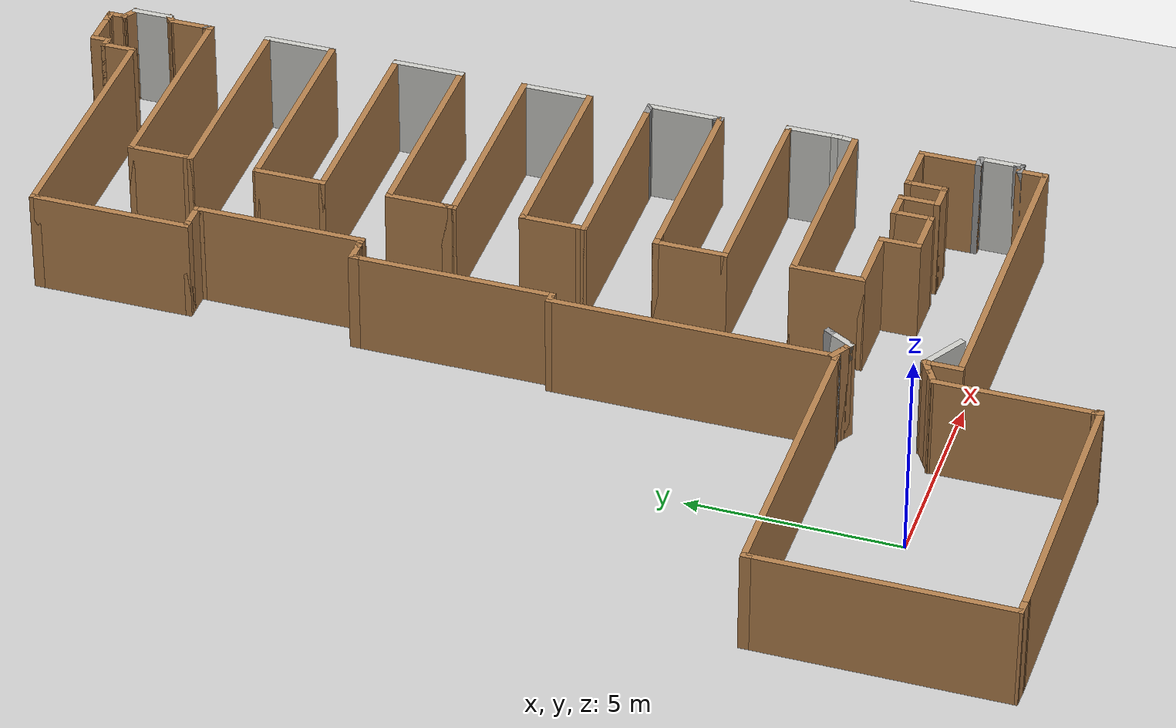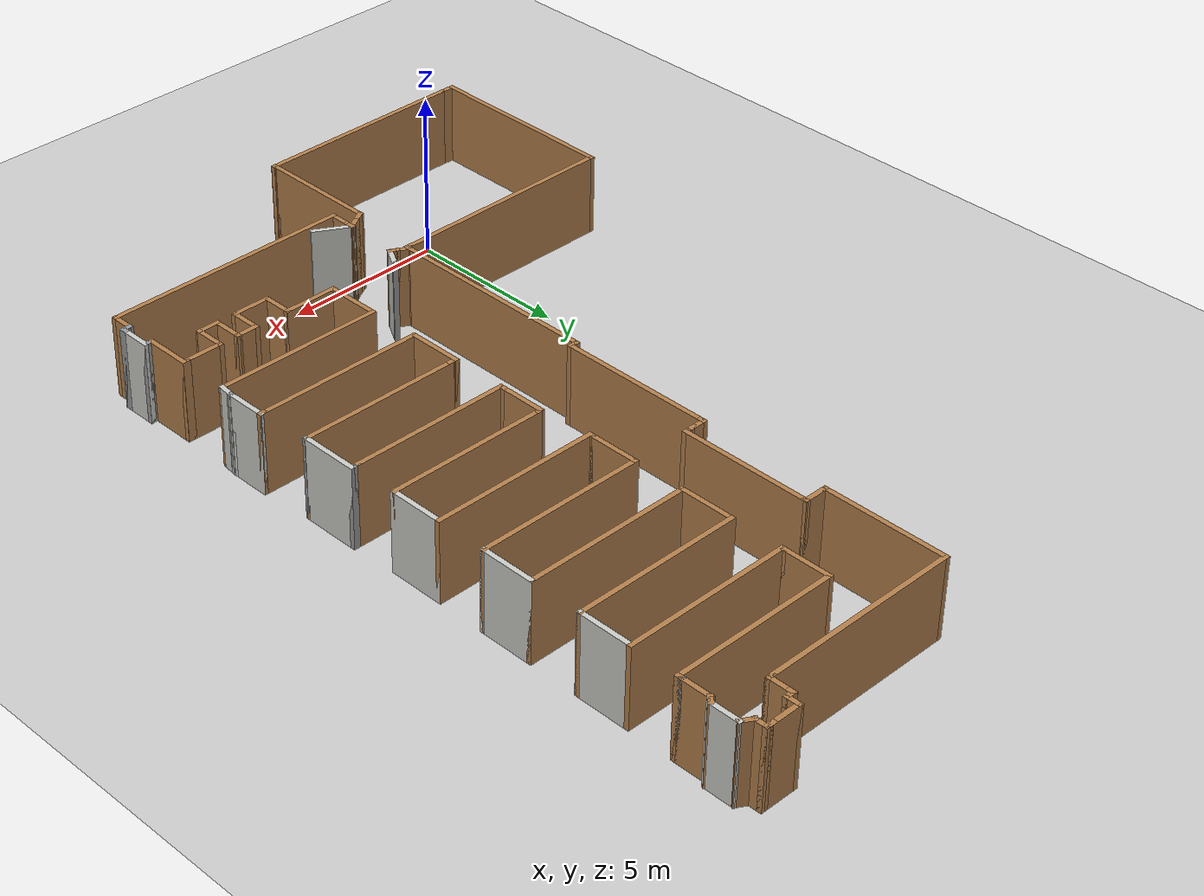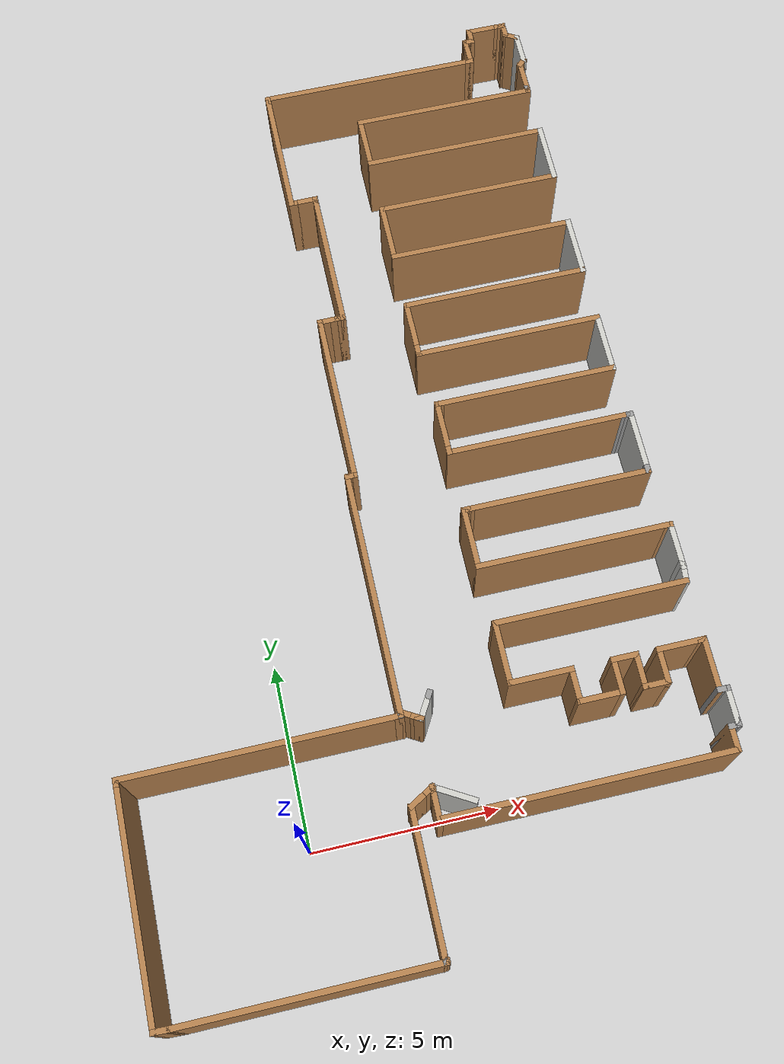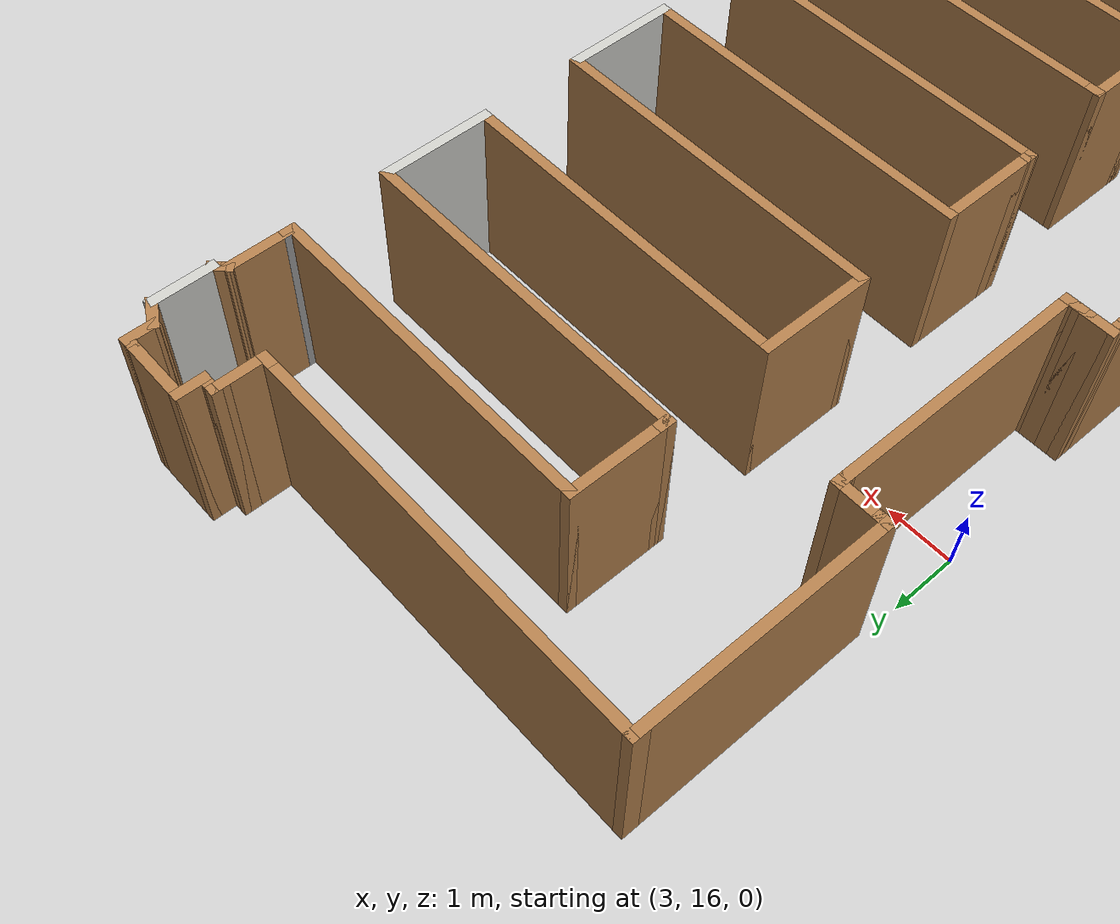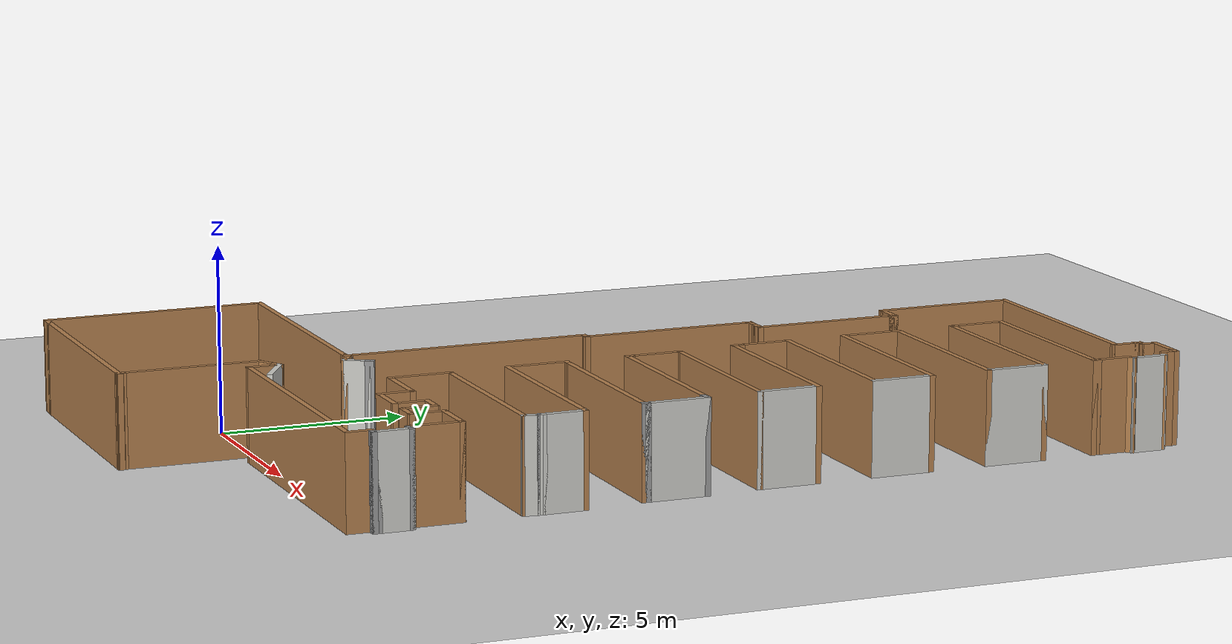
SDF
<sdf version="1.6">
 <world name="default">
  <light name="sun" type="directional">
   <pose>0 0 10 0 -0 0</pose>
   <diffuse>0.8 0.8 0.8 1</diffuse>
   <specular>0.2 0.2 0.2 1</specular>
   <attenuation>
    <range>1000</range>
    <constant>0.9</constant>
    <linear>0.01</linear>
    <quadratic>0.001</quadratic>
   </attenuation>
   <direction>-0.5 0.1 -0.9</direction>
  </light>
  <model name="ground_plane">
   <static>1</static>
   <link name="link">
    <collision name="collision">
     <geometry><plane><normal>0 0 1</normal><size>100 100</size></plane></geometry>
     <surface>
      <contact><collide_bitmask>65535</collide_bitmask></contact>
      <friction><ode><mu>100</mu><mu2>50</mu2></ode></friction>
     </surface>
    </collision>
    <visual name="visual">
     <cast_shadows>0</cast_shadows>
     <geometry><plane><normal>0 0 1</normal><size>100 100</size></plane></geometry>
     <material>
      <script><uri>file://media/materials/scripts/gazebo.material</uri><name>Gazebo/Grey</name></script>
     </material>
    </visual>
   </link>
  </model>
  <gravity>0 0 -9.8</gravity>
  <magnetic_field>6e-06 2.3e-05 -4.2e-05</magnetic_field>
  <atmosphere type="adiabatic"/>
  <physics name="default_physics" default="0" type="ode">
   <max_step_size>0.001</max_step_size>
   <real_time_factor>1</real_time_factor>
   <real_time_update_rate>1000</real_time_update_rate>
  </physics>
  <scene><ambient>0.4 0.4 0.4 1</ambient><background>0.7 0.7 0.7 1</background><shadows>1</shadows></scene>
  <audio><device>default</device></audio>
  <spherical_coordinates>
   <surface_model>EARTH_WGS84</surface_model>
   <latitude_deg>0</latitude_deg>
   <longitude_deg>0</longitude_deg>
   <elevation>0</elevation>
   <heading_deg>0</heading_deg>
  </spherical_coordinates>
  <model name="ecst_v3">
   <pose>3.45571 9.45141 0 0 0 -1.5708</pose>
   <link name="Wall_0">
    <collision name="Wall_0_Collision">
     <geometry><box><size>5.25 0.15 2.5</size></box></geometry>
     <pose>0 0 1.25 0 -0 0</pose>
    </collision>
    <visual name="Wall_0_Visual">
     <pose>0 0 1.25 0 -0 0</pose>
     <geometry><box><size>5.25 0.15 2.5</size></box></geometry>
     <material>
      <script><uri>file://media/materials/scripts/gazebo.material</uri><name>Gazebo/Wood</name></script>
      <ambient>1 1 1 1</ambient>
     </material>
     <meta><layer>0</layer></meta>
    </visual>
    <pose>5.21294 4.93605 0 0 -0 -1.5708</pose>
   </link>
   <link name="Wall_1">
    <collision name="Wall_1_Collision">
     <geometry><box><size>1.75 0.15 2.5</size></box></geometry>
     <pose>0 0 1.25 0 -0 0</pose>
    </collision>
    <visual name="Wall_1_Visual">
     <pose>0 0 1.25 0 -0 0</pose>
     <geometry><box><size>1.75 0.15 2.5</size></box></geometry>
     <material>
      <script><uri>file://media/materials/scripts/gazebo.material</uri><name>Gazebo/Wood</name></script>
      <ambient>1 1 1 1</ambient>
     </material>
     <meta><layer>0</layer></meta>
    </visual>
    <pose>6.01294 2.38605 0 0 -0 0</pose>
   </link>
   <link name="Wall_10">
    <collision name="Wall_10_Collision">
     <geometry><box><size>1.25 0.15 2.5</size></box></geometry>
     <pose>0 0 1.25 0 -0 0</pose>
    </collision>
    <visual name="Wall_10_Visual">
     <pose>0 0 1.25 0 -0 0</pose>
     <geometry><box><size>1.25 0.15 2.5</size></box></geometry>
     <material>
      <script><uri>file://media/materials/scripts/gazebo.material</uri><name>Gazebo/Wood</name></script>
      <ambient>1 1 1 1</ambient>
     </material>
     <meta><layer>0</layer></meta>
    </visual>
    <pose>6.81294 6.83605 0 0 -0 1.5708</pose>
   </link>
   <link name="Wall_100">
    <collision name="Wall_100_Collision">
     <geometry><box><size>5 0.15 2.5</size></box></geometry>
     <pose>0 0 1.25 0 -0 0</pose>
    </collision>
    <visual name="Wall_100_Visual">
     <pose>0 0 1.25 0 -0 0</pose>
     <geometry><box><size>5 0.15 2.5</size></box></geometry>
     <material>
      <script><uri>file://media/materials/scripts/gazebo.material</uri><name>Gazebo/Wood</name></script>
      <ambient>1 1 1 1</ambient>
     </material>
     <meta><layer>0</layer></meta>
    </visual>
    <pose>-1.12064 4.85351 0 0 -0 -1.5708</pose>
   </link>
   <link name="Wall_101">
    <collision name="Wall_101_Collision">
     <geometry><box><size>0.25 0.15 2.5</size></box></geometry>
     <pose>0 0 1.25 0 -0 0</pose>
    </collision>
    <visual name="Wall_101_Visual">
     <pose>0 0 1.25 0 -0 0</pose>
     <geometry><box><size>0.25 0.15 2.5</size></box></geometry>
     <material>
      <script><uri>file://media/materials/scripts/gazebo.material</uri><name>Gazebo/Wood</name></script>
      <ambient>1 1 1 1</ambient>
     </material>
     <meta><layer>0</layer></meta>
    </visual>
    <pose>-1.12064 2.37851 0 0 -0 -1.5708</pose>
   </link>
   <link name="Wall_102">
    <collision name="Wall_102_Collision">
     <geometry><box><size>1.5 0.15 2.5</size></box></geometry>
     <pose>0 0 1.25 0 -0 0</pose>
    </collision>
    <visual name="Wall_102_Visual">
     <pose>0 0 1.25 0 -0 0</pose>
     <geometry><box><size>1.5 0.15 2.5</size></box></geometry>
     <material>
      <script><uri>file://media/materials/scripts/gazebo.material</uri><name>Gazebo/Wood</name></script>
      <ambient>1 1 1 1</ambient>
     </material>
     <meta><layer>0</layer></meta>
    </visual>
    <pose>-0.445642 2.32851 0 0 -0 0</pose>
   </link>
   <link name="Wall_103">
    <collision name="Wall_103_Collision">
     <geometry><box><size>0.25 0.15 2.5</size></box></geometry>
     <pose>0 0 1.25 0 -0 0</pose>
    </collision>
    <visual name="Wall_103_Visual">
     <pose>0 0 1.25 0 -0 0</pose>
     <geometry><box><size>0.25 0.15 2.5</size></box></geometry>
     <material>
      <script><uri>file://media/materials/scripts/gazebo.material</uri><name>Gazebo/Wood</name></script>
      <ambient>1 1 1 1</ambient>
     </material>
     <meta><layer>0</layer></meta>
    </visual>
    <pose>0.279358 2.32851 0 0 -0 0</pose>
   </link>
   <link name="Wall_104">
    <collision name="Wall_104_Collision">
     <geometry><box><size>5 0.15 2.5</size></box></geometry>
     <pose>0 0 1.25 0 -0 0</pose>
    </collision>
    <visual name="Wall_104_Visual">
     <pose>0 0 1.25 0 -0 0</pose>
     <geometry><box><size>5 0.15 2.5</size></box></geometry>
     <material>
      <script><uri>file://media/materials/scripts/gazebo.material</uri><name>Gazebo/Wood</name></script>
      <ambient>1 1 1 1</ambient>
     </material>
     <meta><layer>0</layer></meta>
    </visual>
    <pose>0.329358 4.75351 0 0 -0 1.5708</pose>
   </link>
   <link name="Wall_105">
    <collision name="Wall_105_Collision">
     <geometry><box><size>0.25 0.15 2.5</size></box></geometry>
     <pose>0 0 1.25 0 -0 0</pose>
    </collision>
    <visual name="Wall_105_Visual">
     <pose>0 0 1.25 0 -0 0</pose>
     <geometry><box><size>0.25 0.15 2.5</size></box></geometry>
     <material>
      <script><uri>file://media/materials/scripts/gazebo.material</uri><name>Gazebo/Grey</name></script>
      <ambient>1 1 1 1</ambient>
     </material>
     <meta><layer>0</layer></meta>
    </visual>
    <pose>0.329358 7.22851 0 0 -0 1.5708</pose>
   </link>
   <link name="Wall_106">
    <collision name="Wall_106_Collision">
     <geometry><box><size>0.25 0.15 2.5</size></box></geometry>
     <pose>0 0 1.25 0 -0 0</pose>
    </collision>
    <visual name="Wall_106_Visual">
     <pose>0 0 1.25 0 -0 0</pose>
     <geometry><box><size>0.25 0.15 2.5</size></box></geometry>
     <material>
      <script><uri>file://media/materials/scripts/gazebo.material</uri><name>Gazebo/Grey</name></script>
      <ambient>1 1 1 1</ambient>
     </material>
     <meta><layer>0</layer></meta>
    </visual>
    <pose>0.329358 7.32851 0 0 -0 1.5708</pose>
   </link>
   <link name="Wall_107">
    <collision name="Wall_107_Collision">
     <geometry><box><size>1.75 0.15 2.5</size></box></geometry>
     <pose>0 0 1.25 0 -0 0</pose>
    </collision>
    <visual name="Wall_107_Visual">
     <pose>0 0 1.25 0 -0 0</pose>
     <geometry><box><size>1.75 0.15 2.5</size></box></geometry>
     <material>
      <script><uri>file://media/materials/scripts/gazebo.material</uri><name>Gazebo/CeilingTiled</name></script>
      <ambient>1 1 1 1</ambient>
     </material>
     <meta><layer>0</layer></meta>
    </visual>
    <pose>1.12936 7.37851 0 0 -0 0</pose>
   </link>
   <link name="Wall_108">
    <collision name="Wall_108_Collision">
     <geometry><box><size>0.15 0.15 2.5</size></box></geometry>
     <pose>0 0 1.25 0 -0 0</pose>
    </collision>
    <visual name="Wall_108_Visual">
     <pose>0 0 1.25 0 -0 0</pose>
     <geometry><box><size>0.15 0.15 2.5</size></box></geometry>
     <material>
      <script><uri>file://media/materials/scripts/gazebo.material</uri><name>Gazebo/Grey</name></script>
      <ambient>1 1 1 1</ambient>
     </material>
     <meta><layer>0</layer></meta>
    </visual>
    <pose>1.92936 7.37851 0 0 -0 0</pose>
   </link>
   <link name="Wall_109">
    <collision name="Wall_109_Collision">
     <geometry><box><size>0.25 0.15 2.5</size></box></geometry>
     <pose>0 0 1.25 0 -0 0</pose>
    </collision>
    <visual name="Wall_109_Visual">
     <pose>0 0 1.25 0 -0 0</pose>
     <geometry><box><size>0.25 0.15 2.5</size></box></geometry>
     <material>
      <script><uri>file://media/materials/scripts/gazebo.material</uri><name>Gazebo/Grey</name></script>
      <ambient>1 1 1 1</ambient>
     </material>
     <meta><layer>0</layer></meta>
    </visual>
    <pose>1.97936 7.37851 0 0 -0 0</pose>
   </link>
   <link name="Wall_11">
    <collision name="Wall_11_Collision">
     <geometry><box><size>0.25 0.15 2.5</size></box></geometry>
     <pose>0 0 1.25 0 -0 0</pose>
    </collision>
    <visual name="Wall_11_Visual">
     <pose>0 0 1.25 0 -0 0</pose>
     <geometry><box><size>0.25 0.15 2.5</size></box></geometry>
     <material>
      <script><uri>file://media/materials/scripts/gazebo.material</uri><name>Gazebo/Wood</name></script>
      <ambient>1 1 1 1</ambient>
     </material>
     <meta><layer>0</layer></meta>
    </visual>
    <pose>6.81294 7.43605 0 0 -0 1.5708</pose>
   </link>
   <link name="Wall_110">
    <collision name="Wall_110_Collision">
     <geometry><box><size>5 0.15 2.5</size></box></geometry>
     <pose>0 0 1.25 0 -0 0</pose>
    </collision>
    <visual name="Wall_110_Visual">
     <pose>0 0 1.25 0 -0 0</pose>
     <geometry><box><size>5 0.15 2.5</size></box></geometry>
     <material>
      <script><uri>file://media/materials/scripts/gazebo.material</uri><name>Gazebo/Wood</name></script>
      <ambient>1 1 1 1</ambient>
     </material>
     <meta><layer>0</layer></meta>
    </visual>
    <pose>2.02936 4.95351 0 0 -0 -1.5708</pose>
   </link>
   <link name="Wall_113">
    <collision name="Wall_113_Collision">
     <geometry><box><size>0.25 0.15 2.5</size></box></geometry>
     <pose>0 0 1.25 0 -0 0</pose>
    </collision>
    <visual name="Wall_113_Visual">
     <pose>0 0 1.25 0 -0 0</pose>
     <geometry><box><size>0.25 0.15 2.5</size></box></geometry>
     <material>
      <script><uri>file://media/materials/scripts/gazebo.material</uri><name>Gazebo/Wood</name></script>
      <ambient>1 1 1 1</ambient>
     </material>
     <meta><layer>0</layer></meta>
    </visual>
    <pose>2.02936 2.47851 0 0 -0 -1.5708</pose>
   </link>
   <link name="Wall_114">
    <collision name="Wall_114_Collision">
     <geometry><box><size>0.25 0.15 2.5</size></box></geometry>
     <pose>0 0 1.25 0 -0 0</pose>
    </collision>
    <visual name="Wall_114_Visual">
     <pose>0 0 1.25 0 -0 0</pose>
     <geometry><box><size>0.25 0.15 2.5</size></box></geometry>
     <material>
      <script><uri>file://media/materials/scripts/gazebo.material</uri><name>Gazebo/Wood</name></script>
      <ambient>1 1 1 1</ambient>
     </material>
     <meta><layer>0</layer></meta>
    </visual>
    <pose>2.02936 2.37851 0 0 -0 -1.5708</pose>
   </link>
   <link name="Wall_115">
    <collision name="Wall_115_Collision">
     <geometry><box><size>1.75 0.15 2.5</size></box></geometry>
     <pose>0 0 1.25 0 -0 0</pose>
    </collision>
    <visual name="Wall_115_Visual">
     <pose>0 0 1.25 0 -0 0</pose>
     <geometry><box><size>1.75 0.15 2.5</size></box></geometry>
     <material>
      <script><uri>file://media/materials/scripts/gazebo.material</uri><name>Gazebo/Wood</name></script>
      <ambient>1 1 1 1</ambient>
     </material>
     <meta><layer>0</layer></meta>
    </visual>
    <pose>2.82936 2.32851 0 0 -0 0</pose>
   </link>
   <link name="Wall_116">
    <collision name="Wall_116_Collision">
     <geometry><box><size>5.25 0.15 2.5</size></box></geometry>
     <pose>0 0 1.25 0 -0 0</pose>
    </collision>
    <visual name="Wall_116_Visual">
     <pose>0 0 1.25 0 -0 0</pose>
     <geometry><box><size>5.25 0.15 2.5</size></box></geometry>
     <material>
      <script><uri>file://media/materials/scripts/gazebo.material</uri><name>Gazebo/Wood</name></script>
      <ambient>1 1 1 1</ambient>
     </material>
     <meta><layer>0</layer></meta>
    </visual>
    <pose>3.62936 4.87851 0 0 -0 1.5708</pose>
   </link>
   <link name="Wall_117">
    <collision name="Wall_117_Collision">
     <geometry><box><size>0.25 0.15 2.5</size></box></geometry>
     <pose>0 0 1.25 0 -0 0</pose>
    </collision>
    <visual name="Wall_117_Visual">
     <pose>0 0 1.25 0 -0 0</pose>
     <geometry><box><size>0.25 0.15 2.5</size></box></geometry>
     <material>
      <script><uri>file://media/materials/scripts/gazebo.material</uri><name>Gazebo/Wood</name></script>
      <ambient>1 1 1 1</ambient>
     </material>
     <meta><layer>0</layer></meta>
    </visual>
    <pose>3.62936 7.47851 0 0 -0 1.5708</pose>
   </link>
   <link name="Wall_118">
    <collision name="Wall_118_Collision">
     <geometry><box><size>1.25 0.15 2.5</size></box></geometry>
     <pose>0 0 1.25 0 -0 0</pose>
    </collision>
    <visual name="Wall_118_Visual">
     <pose>0 0 1.25 0 -0 0</pose>
     <geometry><box><size>1.25 0.15 2.5</size></box></geometry>
     <material>
      <script><uri>file://media/materials/scripts/gazebo.material</uri><name>Gazebo/CeilingTiled</name></script>
      <ambient>1 1 1 1</ambient>
     </material>
     <meta><layer>0</layer></meta>
    </visual>
    <pose>4.17936 7.52851 0 0 -0 0</pose>
   </link>
   <link name="Wall_119">
    <collision name="Wall_119_Collision">
     <geometry><box><size>0.25 0.15 2.5</size></box></geometry>
     <pose>0 0 1.25 0 -0 0</pose>
    </collision>
    <visual name="Wall_119_Visual">
     <pose>0 0 1.25 0 -0 0</pose>
     <geometry><box><size>0.25 0.15 2.5</size></box></geometry>
     <material>
      <script><uri>file://media/materials/scripts/gazebo.material</uri><name>Gazebo/CeilingTiled</name></script>
      <ambient>1 1 1 1</ambient>
     </material>
     <meta><layer>0</layer></meta>
    </visual>
    <pose>4.77936 7.52851 0 0 -0 0</pose>
   </link>
   <link name="Wall_12">
    <collision name="Wall_12_Collision">
     <geometry><box><size>1.5 0.15 2.5</size></box></geometry>
     <pose>0 0 1.25 0 -0 0</pose>
    </collision>
    <visual name="Wall_12_Visual">
     <pose>0 0 1.25 0 -0 0</pose>
     <geometry><box><size>1.5 0.15 2.5</size></box></geometry>
     <material>
      <script><uri>file://media/materials/scripts/gazebo.material</uri><name>Gazebo/Wood</name></script>
      <ambient>1 1 1 1</ambient>
     </material>
     <meta><layer>0</layer></meta>
    </visual>
    <pose>7.48794 7.48605 0 0 -0 0</pose>
   </link>
   <link name="Wall_120">
    <collision name="Wall_120_Collision">
     <geometry><box><size>0.15 0.15 2.5</size></box></geometry>
     <pose>0 0 1.25 0 -0 0</pose>
    </collision>
    <visual name="Wall_120_Visual">
     <pose>0 0 1.25 0 -0 0</pose>
     <geometry><box><size>0.15 0.15 2.5</size></box></geometry>
     <material>
      <script><uri>file://media/materials/scripts/gazebo.material</uri><name>Gazebo/Grey</name></script>
      <ambient>1 1 1 1</ambient>
     </material>
     <meta><layer>0</layer></meta>
    </visual>
    <pose>4.82936 7.52851 0 0 -0 0</pose>
   </link>
   <link name="Wall_121">
    <collision name="Wall_121_Collision">
     <geometry><box><size>0.15 0.15 2.5</size></box></geometry>
     <pose>0 0 1.25 0 -0 0</pose>
    </collision>
    <visual name="Wall_121_Visual">
     <pose>0 0 1.25 0 -0 0</pose>
     <geometry><box><size>0.15 0.15 2.5</size></box></geometry>
     <material>
      <script><uri>file://media/materials/scripts/gazebo.material</uri><name>Gazebo/CeilingTiled</name></script>
      <ambient>1 1 1 1</ambient>
     </material>
     <meta><layer>0</layer></meta>
    </visual>
    <pose>4.82936 7.52851 0 0 -0 0</pose>
   </link>
   <link name="Wall_122">
    <collision name="Wall_122_Collision">
     <geometry><box><size>0.535922 0.15 2.5</size></box></geometry>
     <pose>0 0 1.25 0 -0 0</pose>
    </collision>
    <visual name="Wall_122_Visual">
     <pose>0 0 1.25 0 -0 0</pose>
     <geometry><box><size>0.535922 0.15 2.5</size></box></geometry>
     <material>
      <script><uri>file://media/materials/scripts/gazebo.material</uri><name>Gazebo/CeilingTiled</name></script>
      <ambient>1 1 1 1</ambient>
     </material>
     <meta><layer>0</layer></meta>
    </visual>
    <pose>5.02115 7.50728 0 0 -0 -0.110265</pose>
   </link>
   <link name="Wall_126">
    <collision name="Wall_126_Collision">
     <geometry><box><size>0.15 0.15 2.5</size></box></geometry>
     <pose>0 0 1.25 0 -0 0</pose>
    </collision>
    <visual name="Wall_126_Visual">
     <pose>0 0 1.25 0 -0 0</pose>
     <geometry><box><size>0.15 0.15 2.5</size></box></geometry>
     <material>
      <script><uri>file://media/materials/scripts/gazebo.material</uri><name>Gazebo/Grey</name></script>
      <ambient>1 1 1 1</ambient>
     </material>
     <meta><layer>0</layer></meta>
    </visual>
    <pose>7.01294 -0.483173 0 0 -0 0</pose>
   </link>
   <link name="Wall_127">
    <collision name="Wall_127_Collision">
     <geometry><box><size>0.15 0.15 2.5</size></box></geometry>
     <pose>0 0 1.25 0 -0 0</pose>
    </collision>
    <visual name="Wall_127_Visual">
     <pose>0 0 1.25 0 -0 0</pose>
     <geometry><box><size>0.15 0.15 2.5</size></box></geometry>
     <material>
      <script><uri>file://media/materials/scripts/gazebo.material</uri><name>Gazebo/Grey</name></script>
      <ambient>1 1 1 1</ambient>
     </material>
     <meta><layer>0</layer></meta>
    </visual>
    <pose>7.01294 -0.483173 0 0 -0 0</pose>
   </link>
   <link name="Wall_128">
    <collision name="Wall_128_Collision">
     <geometry><box><size>0.15 0.15 2.5</size></box></geometry>
     <pose>0 0 1.25 0 -0 0</pose>
    </collision>
    <visual name="Wall_128_Visual">
     <pose>0 0 1.25 0 -0 0</pose>
     <geometry><box><size>0.15 0.15 2.5</size></box></geometry>
     <material>
      <script><uri>file://media/materials/scripts/gazebo.material</uri><name>Gazebo/Grey</name></script>
      <ambient>1 1 1 1</ambient>
     </material>
     <meta><layer>0</layer></meta>
    </visual>
    <pose>7.01294 -0.483173 0 0 -0 0</pose>
   </link>
   <link name="Wall_129">
    <collision name="Wall_129_Collision">
     <geometry><box><size>0.25 0.15 2.5</size></box></geometry>
     <pose>0 0 1.25 0 -0 0</pose>
    </collision>
    <visual name="Wall_129_Visual">
     <pose>0 0 1.25 0 -0 0</pose>
     <geometry><box><size>0.25 0.15 2.5</size></box></geometry>
     <material>
      <script><uri>file://media/materials/scripts/gazebo.material</uri><name>Gazebo/Wood</name></script>
      <ambient>1 1 1 1</ambient>
     </material>
     <meta><layer>0</layer></meta>
    </visual>
    <pose>6.96294 -0.483173 0 0 -0 3.14159</pose>
   </link>
   <link name="Wall_13">
    <collision name="Wall_13_Collision">
     <geometry><box><size>0.25 0.15 2.5</size></box></geometry>
     <pose>0 0 1.25 0 -0 0</pose>
    </collision>
    <visual name="Wall_13_Visual">
     <pose>0 0 1.25 0 -0 0</pose>
     <geometry><box><size>0.25 0.15 2.5</size></box></geometry>
     <material>
      <script><uri>file://media/materials/scripts/gazebo.material</uri><name>Gazebo/Grey</name></script>
      <ambient>1 1 1 1</ambient>
     </material>
     <meta><layer>0</layer></meta>
    </visual>
    <pose>8.16294 7.53605 0 0 -0 1.5708</pose>
   </link>
   <link name="Wall_130">
    <collision name="Wall_130_Collision">
     <geometry><box><size>0.16 0.15 2.5</size></box></geometry>
     <pose>0 0 1.25 0 -0 0</pose>
    </collision>
    <visual name="Wall_130_Visual">
     <pose>0 0 1.25 0 -0 0</pose>
     <geometry><box><size>0.16 0.15 2.5</size></box></geometry>
     <material>
      <script><uri>file://media/materials/scripts/gazebo.material</uri><name>Gazebo/Grey</name></script>
      <ambient>1 1 1 1</ambient>
     </material>
     <meta><layer>0</layer></meta>
    </visual>
    <pose>6.91794 -0.483173 0 0 -0 0</pose>
   </link>
   <link name="Wall_131">
    <collision name="Wall_131_Collision">
     <geometry><box><size>0.5 0.15 2.5</size></box></geometry>
     <pose>0 0 1.25 0 -0 0</pose>
    </collision>
    <visual name="Wall_131_Visual">
     <pose>0 0 1.25 0 -0 0</pose>
     <geometry><box><size>0.5 0.15 2.5</size></box></geometry>
     <material>
      <script><uri>file://media/materials/scripts/gazebo.material</uri><name>Gazebo/Wood</name></script>
      <ambient>1 1 1 1</ambient>
     </material>
     <meta><layer>0</layer></meta>
    </visual>
    <pose>7.01044 -0.331619 0 0 -0 1.0472</pose>
   </link>
   <link name="Wall_132">
    <collision name="Wall_132_Collision">
     <geometry><box><size>0.25 0.15 2.5</size></box></geometry>
     <pose>0 0 1.25 0 -0 0</pose>
    </collision>
    <visual name="Wall_132_Visual">
     <pose>0 0 1.25 0 -0 0</pose>
     <geometry><box><size>0.25 0.15 2.5</size></box></geometry>
     <material>
      <script><uri>file://media/materials/scripts/gazebo.material</uri><name>Gazebo/Wood</name></script>
      <ambient>1 1 1 1</ambient>
     </material>
     <meta><layer>0</layer></meta>
    </visual>
    <pose>7.12294 -0.136763 0 0 -0 1.0472</pose>
   </link>
   <link name="Wall_133">
    <collision name="Wall_133_Collision">
     <geometry><box><size>0.25 0.15 2.5</size></box></geometry>
     <pose>0 0 1.25 0 -0 0</pose>
    </collision>
    <visual name="Wall_133_Visual">
     <pose>0 0 1.25 0 -0 0</pose>
     <geometry><box><size>0.25 0.15 2.5</size></box></geometry>
     <material>
      <script><uri>file://media/materials/scripts/gazebo.material</uri><name>Gazebo/Wood</name></script>
      <ambient>1 1 1 1</ambient>
     </material>
     <meta><layer>0</layer></meta>
    </visual>
    <pose>7.17294 -0.050161 0 0 -0 1.0472</pose>
   </link>
   <link name="Wall_134">
    <collision name="Wall_134_Collision">
     <geometry><box><size>0.75 0.15 2.5</size></box></geometry>
     <pose>0 0 1.25 0 -0 0</pose>
    </collision>
    <visual name="Wall_134_Visual">
     <pose>0 0 1.25 0 -0 0</pose>
     <geometry><box><size>0.75 0.15 2.5</size></box></geometry>
     <material>
      <script><uri>file://media/materials/scripts/gazebo.material</uri><name>Gazebo/CeilingTiled</name></script>
      <ambient>1 1 1 1</ambient>
     </material>
     <meta><layer>0</layer></meta>
    </visual>
    <pose>6.93813 0.14314 0 0 -0 2.61799</pose>
   </link>
   <link name="Wall_135">
    <collision name="Wall_135_Collision">
     <geometry><box><size>0.25 0.15 2.5</size></box></geometry>
     <pose>0 0 1.25 0 -0 0</pose>
    </collision>
    <visual name="Wall_135_Visual">
     <pose>0 0 1.25 0 -0 0</pose>
     <geometry><box><size>0.25 0.15 2.5</size></box></geometry>
     <material>
      <script><uri>file://media/materials/scripts/gazebo.material</uri><name>Gazebo/Grey</name></script>
      <ambient>1 1 1 1</ambient>
     </material>
     <meta><layer>0</layer></meta>
    </visual>
    <pose>6.63502 0.318141 0 0 -0 2.61799</pose>
   </link>
   <link name="Wall_14">
    <collision name="Wall_14_Collision">
     <geometry><box><size>0.25 0.15 2.5</size></box></geometry>
     <pose>0 0 1.25 0 -0 0</pose>
    </collision>
    <visual name="Wall_14_Visual">
     <pose>0 0 1.25 0 -0 0</pose>
     <geometry><box><size>0.25 0.15 2.5</size></box></geometry>
     <material>
      <script><uri>file://media/materials/scripts/gazebo.material</uri><name>Gazebo/Grey</name></script>
      <ambient>1 1 1 1</ambient>
     </material>
     <meta><layer>0</layer></meta>
    </visual>
    <pose>8.16294 7.63605 0 0 -0 1.5708</pose>
   </link>
   <link name="Wall_15">
    <collision name="Wall_15_Collision">
     <geometry><box><size>1 0.15 2.5</size></box></geometry>
     <pose>0 0 1.25 0 -0 0</pose>
    </collision>
    <visual name="Wall_15_Visual">
     <pose>0 0 1.25 0 -0 0</pose>
     <geometry><box><size>1 0.15 2.5</size></box></geometry>
     <material>
      <script><uri>file://media/materials/scripts/gazebo.material</uri><name>Gazebo/CeilingTiled</name></script>
      <ambient>1 1 1 1</ambient>
     </material>
     <meta><layer>0</layer></meta>
    </visual>
    <pose>8.58794 7.68605 0 0 -0 0</pose>
   </link>
   <link name="Wall_16">
    <collision name="Wall_16_Collision">
     <geometry><box><size>0.25 0.15 2.5</size></box></geometry>
     <pose>0 0 1.25 0 -0 0</pose>
    </collision>
    <visual name="Wall_16_Visual">
     <pose>0 0 1.25 0 -0 0</pose>
     <geometry><box><size>0.25 0.15 2.5</size></box></geometry>
     <material>
      <script><uri>file://media/materials/scripts/gazebo.material</uri><name>Gazebo/Grey</name></script>
      <ambient>1 1 1 1</ambient>
     </material>
     <meta><layer>0</layer></meta>
    </visual>
    <pose>9.06294 7.68605 0 0 -0 0</pose>
   </link>
   <link name="Wall_17">
    <collision name="Wall_17_Collision">
     <geometry><box><size>0.25 0.15 2.5</size></box></geometry>
     <pose>0 0 1.25 0 -0 0</pose>
    </collision>
    <visual name="Wall_17_Visual">
     <pose>0 0 1.25 0 -0 0</pose>
     <geometry><box><size>0.25 0.15 2.5</size></box></geometry>
     <material>
      <script><uri>file://media/materials/scripts/gazebo.material</uri><name>Gazebo/Grey</name></script>
      <ambient>1 1 1 1</ambient>
     </material>
     <meta><layer>0</layer></meta>
    </visual>
    <pose>9.11294 7.63605 0 0 -0 -1.5708</pose>
   </link>
   <link name="Wall_18">
    <collision name="Wall_18_Collision">
     <geometry><box><size>0.25 0.15 2.5</size></box></geometry>
     <pose>0 0 1.25 0 -0 0</pose>
    </collision>
    <visual name="Wall_18_Visual">
     <pose>0 0 1.25 0 -0 0</pose>
     <geometry><box><size>0.25 0.15 2.5</size></box></geometry>
     <material>
      <script><uri>file://media/materials/scripts/gazebo.material</uri><name>Gazebo/Grey</name></script>
      <ambient>1 1 1 1</ambient>
     </material>
     <meta><layer>0</layer></meta>
    </visual>
    <pose>9.11294 7.53605 0 0 -0 -1.5708</pose>
   </link>
   <link name="Wall_19">
    <collision name="Wall_19_Collision">
     <geometry><box><size>0.75 0.15 2.5</size></box></geometry>
     <pose>0 0 1.25 0 -0 0</pose>
    </collision>
    <visual name="Wall_19_Visual">
     <pose>0 0 1.25 0 -0 0</pose>
     <geometry><box><size>0.75 0.15 2.5</size></box></geometry>
     <material>
      <script><uri>file://media/materials/scripts/gazebo.material</uri><name>Gazebo/Wood</name></script>
      <ambient>1 1 1 1</ambient>
     </material>
     <meta><layer>0</layer></meta>
    </visual>
    <pose>9.41294 7.48605 0 0 -0 0</pose>
   </link>
   <link name="Wall_2">
    <collision name="Wall_2_Collision">
     <geometry><box><size>1.75 0.15 2.5</size></box></geometry>
     <pose>0 0 1.25 0 -0 0</pose>
    </collision>
    <visual name="Wall_2_Visual">
     <pose>0 0 1.25 0 -0 0</pose>
     <geometry><box><size>1.75 0.15 2.5</size></box></geometry>
     <material>
      <script><uri>file://media/materials/scripts/gazebo.material</uri><name>Gazebo/Wood</name></script>
      <ambient>1 1 1 1</ambient>
     </material>
     <meta><layer>0</layer></meta>
    </visual>
    <pose>6.81294 3.18605 0 0 -0 1.5708</pose>
   </link>
   <link name="Wall_20">
    <collision name="Wall_20_Collision">
     <geometry><box><size>7.75 0.15 2.5</size></box></geometry>
     <pose>0 0 1.25 0 -0 0</pose>
    </collision>
    <visual name="Wall_20_Visual">
     <pose>0 0 1.25 0 -0 0</pose>
     <geometry><box><size>7.75 0.15 2.5</size></box></geometry>
     <material>
      <script><uri>file://media/materials/scripts/gazebo.material</uri><name>Gazebo/Wood</name></script>
      <ambient>1 1 1 1</ambient>
     </material>
     <meta><layer>0</layer></meta>
    </visual>
    <pose>9.71294 3.68605 0 0 -0 -1.5708</pose>
   </link>
   <link name="Wall_21">
    <collision name="Wall_21_Collision">
     <geometry><box><size>0.75 0.15 2.5</size></box></geometry>
     <pose>0 0 1.25 0 -0 0</pose>
    </collision>
    <visual name="Wall_21_Visual">
     <pose>0 0 1.25 0 -0 0</pose>
     <geometry><box><size>0.75 0.15 2.5</size></box></geometry>
     <material>
      <script><uri>file://media/materials/scripts/gazebo.material</uri><name>Gazebo/Wood</name></script>
      <ambient>1 1 1 1</ambient>
     </material>
     <meta><layer>0</layer></meta>
    </visual>
    <pose>9.41294 -0.113953 0 0 -0 3.14159</pose>
   </link>
   <link name="Wall_22">
    <collision name="Wall_22_Collision">
     <geometry><box><size>0.25 0.15 2.5</size></box></geometry>
     <pose>0 0 1.25 0 -0 0</pose>
    </collision>
    <visual name="Wall_22_Visual">
     <pose>0 0 1.25 0 -0 0</pose>
     <geometry><box><size>0.25 0.15 2.5</size></box></geometry>
     <material>
      <script><uri>file://media/materials/scripts/gazebo.material</uri><name>Gazebo/Wood</name></script>
      <ambient>1 1 1 1</ambient>
     </material>
     <meta><layer>0</layer></meta>
    </visual>
    <pose>9.06294 -0.113953 0 0 -0 3.14159</pose>
   </link>
   <link name="Wall_23">
    <collision name="Wall_23_Collision">
     <geometry><box><size>0.25 0.15 2.5</size></box></geometry>
     <pose>0 0 1.25 0 -0 0</pose>
    </collision>
    <visual name="Wall_23_Visual">
     <pose>0 0 1.25 0 -0 0</pose>
     <geometry><box><size>0.25 0.15 2.5</size></box></geometry>
     <material>
      <script><uri>file://media/materials/scripts/gazebo.material</uri><name>Gazebo/Wood</name></script>
      <ambient>1 1 1 1</ambient>
     </material>
     <meta><layer>0</layer></meta>
    </visual>
    <pose>8.96294 -0.113953 0 0 -0 3.14159</pose>
   </link>
   <link name="Wall_24">
    <collision name="Wall_24_Collision">
     <geometry><box><size>1.25 0.15 2.5</size></box></geometry>
     <pose>0 0 1.25 0 -0 0</pose>
    </collision>
    <visual name="Wall_24_Visual">
     <pose>0 0 1.25 0 -0 0</pose>
     <geometry><box><size>1.25 0.15 2.5</size></box></geometry>
     <material>
      <script><uri>file://media/materials/scripts/gazebo.material</uri><name>Gazebo/CeilingTiled</name></script>
      <ambient>1 1 1 1</ambient>
     </material>
     <meta><layer>0</layer></meta>
    </visual>
    <pose>9.18794 0.36236 0 0 -0 1.0472</pose>
   </link>
   <link name="Wall_26">
    <collision name="Wall_26_Collision">
     <geometry><box><size>0.5 0.15 2.5</size></box></geometry>
     <pose>0 0 1.25 0 -0 0</pose>
    </collision>
    <visual name="Wall_26_Visual">
     <pose>0 0 1.25 0 -0 0</pose>
     <geometry><box><size>0.5 0.15 2.5</size></box></geometry>
     <material>
      <script><uri>file://media/materials/scripts/gazebo.material</uri><name>Gazebo/Wood</name></script>
      <ambient>1 1 1 1</ambient>
     </material>
     <meta><layer>0</layer></meta>
    </visual>
    <pose>9.00044 -0.265508 0 0 -0 -1.0472</pose>
   </link>
   <link name="Wall_27">
    <collision name="Wall_27_Collision">
     <geometry><box><size>0.5 0.15 2.5</size></box></geometry>
     <pose>0 0 1.25 0 -0 0</pose>
    </collision>
    <visual name="Wall_27_Visual">
     <pose>0 0 1.25 0 -0 0</pose>
     <geometry><box><size>0.5 0.15 2.5</size></box></geometry>
     <material>
      <script><uri>file://media/materials/scripts/gazebo.material</uri><name>Gazebo/Wood</name></script>
      <ambient>1 1 1 1</ambient>
     </material>
     <meta><layer>0</layer></meta>
    </visual>
    <pose>9.17544 -0.568617 0 0 -0 -1.0472</pose>
   </link>
   <link name="Wall_28">
    <collision name="Wall_28_Collision">
     <geometry><box><size>3.75 0.15 2.5</size></box></geometry>
     <pose>0 0 1.25 0 -0 0</pose>
    </collision>
    <visual name="Wall_28_Visual">
     <pose>0 0 1.25 0 -0 0</pose>
     <geometry><box><size>3.75 0.15 2.5</size></box></geometry>
     <material>
      <script><uri>file://media/materials/scripts/gazebo.material</uri><name>Gazebo/Wood</name></script>
      <ambient>1 1 1 1</ambient>
     </material>
     <meta><layer>0</layer></meta>
    </visual>
    <pose>11.0629 -0.720171 0 0 -0 0</pose>
   </link>
   <link name="Wall_29">
    <collision name="Wall_29_Collision">
     <geometry><box><size>0.15 0.15 2.5</size></box></geometry>
     <pose>0 0 1.25 0 -0 0</pose>
    </collision>
    <visual name="Wall_29_Visual">
     <pose>0 0 1.25 0 -0 0</pose>
     <geometry><box><size>0.15 0.15 2.5</size></box></geometry>
     <material>
      <script><uri>file://media/materials/scripts/gazebo.material</uri><name>Gazebo/Wood</name></script>
      <ambient>1 1 1 1</ambient>
     </material>
     <meta><layer>0</layer></meta>
    </visual>
    <pose>12.8629 -0.720171 0 0 -0 0</pose>
   </link>
   <link name="Wall_3">
    <collision name="Wall_3_Collision">
     <geometry><box><size>1 0.15 2.5</size></box></geometry>
     <pose>0 0 1.25 0 -0 0</pose>
    </collision>
    <visual name="Wall_3_Visual">
     <pose>0 0 1.25 0 -0 0</pose>
     <geometry><box><size>1 0.15 2.5</size></box></geometry>
     <material>
      <script><uri>file://media/materials/scripts/gazebo.material</uri><name>Gazebo/Wood</name></script>
      <ambient>1 1 1 1</ambient>
     </material>
     <meta><layer>0</layer></meta>
    </visual>
    <pose>7.23794 3.98605 0 0 -0 0</pose>
   </link>
   <link name="Wall_30">
    <collision name="Wall_30_Collision">
     <geometry><box><size>0.266016 0.15 2.5</size></box></geometry>
     <pose>0 0 1.25 0 -0 0</pose>
    </collision>
    <visual name="Wall_30_Visual">
     <pose>0 0 1.25 0 -0 0</pose>
     <geometry><box><size>0.266016 0.15 2.5</size></box></geometry>
     <material>
      <script><uri>file://media/materials/scripts/gazebo.material</uri><name>Gazebo/Wood</name></script>
      <ambient>1 1 1 1</ambient>
     </material>
     <meta><layer>0</layer></meta>
    </visual>
    <pose>12.9205 -0.712652 0 0 -0 0.129981</pose>
   </link>
   <link name="Wall_31">
    <collision name="Wall_31_Collision">
     <geometry><box><size>6.72196 0.15 2.5</size></box></geometry>
     <pose>0 0 1.25 0 -0 0</pose>
    </collision>
    <visual name="Wall_31_Visual">
     <pose>0 0 1.25 0 -0 0</pose>
     <geometry><box><size>6.72196 0.15 2.5</size></box></geometry>
     <material>
      <script><uri>file://media/materials/scripts/gazebo.material</uri><name>Gazebo/Wood</name></script>
      <ambient>1 1 1 1</ambient>
     </material>
     <meta><layer>0</layer></meta>
    </visual>
    <pose>12.978 -4.00615 0 0 -0 -1.5708</pose>
   </link>
   <link name="Wall_32">
    <collision name="Wall_32_Collision">
     <geometry><box><size>0.534835 0.15 2.5</size></box></geometry>
     <pose>0 0 1.25 0 -0 0</pose>
    </collision>
    <visual name="Wall_32_Visual">
     <pose>0 0 1.25 0 -0 0</pose>
     <geometry><box><size>0.534835 0.15 2.5</size></box></geometry>
     <material>
      <script><uri>file://media/materials/scripts/gazebo.material</uri><name>Gazebo/Wood</name></script>
      <ambient>1 1 1 1</ambient>
     </material>
     <meta><layer>0</layer></meta>
    </visual>
    <pose>12.9705 -7.4909 0 0 -0 -1.60988</pose>
   </link>
   <link name="Wall_38">
    <collision name="Wall_38_Collision">
     <geometry><box><size>0.15 0.15 2.5</size></box></geometry>
     <pose>0 0 1.25 0 -0 0</pose>
    </collision>
    <visual name="Wall_38_Visual">
     <pose>0 0 1.25 0 -0 0</pose>
     <geometry><box><size>0.15 0.15 2.5</size></box></geometry>
     <material>
      <script><uri>file://media/materials/scripts/gazebo.material</uri><name>Gazebo/Wood</name></script>
      <ambient>1 1 1 1</ambient>
     </material>
     <meta><layer>0</layer></meta>
    </visual>
    <pose>12.9527 -0.687517 0 0 -0 0</pose>
   </link>
   <link name="Wall_4">
    <collision name="Wall_4_Collision">
     <geometry><box><size>1.25 0.15 2.5</size></box></geometry>
     <pose>0 0 1.25 0 -0 0</pose>
    </collision>
    <visual name="Wall_4_Visual">
     <pose>0 0 1.25 0 -0 0</pose>
     <geometry><box><size>1.25 0.15 2.5</size></box></geometry>
     <material>
      <script><uri>file://media/materials/scripts/gazebo.material</uri><name>Gazebo/Wood</name></script>
      <ambient>1 1 1 1</ambient>
     </material>
     <meta><layer>0</layer></meta>
    </visual>
    <pose>7.66294 4.53605 0 0 -0 1.5708</pose>
   </link>
   <link name="Wall_42">
    <collision name="Wall_42_Collision">
     <geometry><box><size>0.15 0.15 2.5</size></box></geometry>
     <pose>0 0 1.25 0 -0 0</pose>
    </collision>
    <visual name="Wall_42_Visual">
     <pose>0 0 1.25 0 -0 0</pose>
     <geometry><box><size>0.15 0.15 2.5</size></box></geometry>
     <material>
      <script><uri>file://media/materials/scripts/gazebo.material</uri><name>Gazebo/Grey</name></script>
      <ambient>0 0 0 1</ambient>
     </material>
     <meta><layer>0</layer></meta>
    </visual>
    <pose>12.9678 -0.702555 0 0 -0 0</pose>
   </link>
   <link name="Wall_45">
    <collision name="Wall_45_Collision">
     <geometry><box><size>6 0.15 2.5</size></box></geometry>
     <pose>0 0 1.25 0 -0 0</pose>
    </collision>
    <visual name="Wall_45_Visual">
     <pose>0 0 1.25 0 -0 0</pose>
     <geometry><box><size>6 0.15 2.5</size></box></geometry>
     <material>
      <script><uri>file://media/materials/scripts/gazebo.material</uri><name>Gazebo/Wood</name></script>
      <ambient>1 1 1 1</ambient>
     </material>
     <meta><layer>0</layer></meta>
    </visual>
    <pose>10.0379 -7.68317 0 0 -0 3.14159</pose>
   </link>
   <link name="Wall_46">
    <collision name="Wall_46_Collision">
     <geometry><box><size>0.25 0.15 2.5</size></box></geometry>
     <pose>0 0 1.25 0 -0 0</pose>
    </collision>
    <visual name="Wall_46_Visual">
     <pose>0 0 1.25 0 -0 0</pose>
     <geometry><box><size>0.25 0.15 2.5</size></box></geometry>
     <material>
      <script><uri>file://media/materials/scripts/gazebo.material</uri><name>Gazebo/Wood</name></script>
      <ambient>1 1 1 1</ambient>
     </material>
     <meta><layer>0</layer></meta>
    </visual>
    <pose>7.06294 -7.68317 0 0 -0 3.14159</pose>
   </link>
   <link name="Wall_47">
    <collision name="Wall_47_Collision">
     <geometry><box><size>7.25 0.15 2.5</size></box></geometry>
     <pose>0 0 1.25 0 -0 0</pose>
    </collision>
    <visual name="Wall_47_Visual">
     <pose>0 0 1.25 0 -0 0</pose>
     <geometry><box><size>7.25 0.15 2.5</size></box></geometry>
     <material>
      <script><uri>file://media/materials/scripts/gazebo.material</uri><name>Gazebo/Wood</name></script>
      <ambient>1 1 1 1</ambient>
     </material>
     <meta><layer>0</layer></meta>
    </visual>
    <pose>7.01294 -4.13317 0 0 -0 1.5708</pose>
   </link>
   <link name="Wall_48">
    <collision name="Wall_48_Collision">
     <geometry><box><size>0.25 0.15 2.5</size></box></geometry>
     <pose>0 0 1.25 0 -0 0</pose>
    </collision>
    <visual name="Wall_48_Visual">
     <pose>0 0 1.25 0 -0 0</pose>
     <geometry><box><size>0.25 0.15 2.5</size></box></geometry>
     <material>
      <script><uri>file://media/materials/scripts/gazebo.material</uri><name>Gazebo/Wood</name></script>
      <ambient>1 1 1 1</ambient>
     </material>
     <meta><layer>0</layer></meta>
    </visual>
    <pose>7.01294 -0.533174 0 0 -0 1.5708</pose>
   </link>
   <link name="Wall_49">
    <collision name="Wall_49_Collision">
     <geometry><box><size>6.75 0.15 2.5</size></box></geometry>
     <pose>0 0 1.25 0 -0 0</pose>
    </collision>
    <visual name="Wall_49_Visual">
     <pose>0 0 1.25 0 -0 0</pose>
     <geometry><box><size>6.75 0.15 2.5</size></box></geometry>
     <material>
      <script><uri>file://media/materials/scripts/gazebo.material</uri><name>Gazebo/Wood</name></script>
      <ambient>1 1 1 1</ambient>
     </material>
     <meta><layer>0</layer></meta>
    </visual>
    <pose>3.71294 -0.483173 0 0 -0 3.14159</pose>
   </link>
   <link name="Wall_5">
    <collision name="Wall_5_Collision">
     <geometry><box><size>1 0.15 2.5</size></box></geometry>
     <pose>0 0 1.25 0 -0 0</pose>
    </collision>
    <visual name="Wall_5_Visual">
     <pose>0 0 1.25 0 -0 0</pose>
     <geometry><box><size>1 0.15 2.5</size></box></geometry>
     <material>
      <script><uri>file://media/materials/scripts/gazebo.material</uri><name>Gazebo/Wood</name></script>
      <ambient>1 1 1 1</ambient>
     </material>
     <meta><layer>0</layer></meta>
    </visual>
    <pose>7.23794 5.08605 0 0 -0 3.14159</pose>
   </link>
   <link name="Wall_50">
    <collision name="Wall_50_Collision">
     <geometry><box><size>0.25 0.15 2.5</size></box></geometry>
     <pose>0 0 1.25 0 -0 0</pose>
    </collision>
    <visual name="Wall_50_Visual">
     <pose>0 0 1.25 0 -0 0</pose>
     <geometry><box><size>0.25 0.15 2.5</size></box></geometry>
     <material>
      <script><uri>file://media/materials/scripts/gazebo.material</uri><name>Gazebo/Wood</name></script>
      <ambient>1 1 1 1</ambient>
     </material>
     <meta><layer>0</layer></meta>
    </visual>
    <pose>0.412937 -0.433174 0 0 -0 1.5708</pose>
   </link>
   <link name="Wall_51">
    <collision name="Wall_51_Collision">
     <geometry><box><size>0.25 0.15 2.5</size></box></geometry>
     <pose>0 0 1.25 0 -0 0</pose>
    </collision>
    <visual name="Wall_51_Visual">
     <pose>0 0 1.25 0 -0 0</pose>
     <geometry><box><size>0.25 0.15 2.5</size></box></geometry>
     <material>
      <script><uri>file://media/materials/scripts/gazebo.material</uri><name>Gazebo/Wood</name></script>
      <ambient>1 1 1 1</ambient>
     </material>
     <meta><layer>0</layer></meta>
    </visual>
    <pose>0.412937 -0.333174 0 0 -0 1.5708</pose>
   </link>
   <link name="Wall_52">
    <collision name="Wall_52_Collision">
     <geometry><box><size>4.75 0.15 2.5</size></box></geometry>
     <pose>0 0 1.25 0 -0 0</pose>
    </collision>
    <visual name="Wall_52_Visual">
     <pose>0 0 1.25 0 -0 0</pose>
     <geometry><box><size>4.75 0.15 2.5</size></box></geometry>
     <material>
      <script><uri>file://media/materials/scripts/gazebo.material</uri><name>Gazebo/Wood</name></script>
      <ambient>1 1 1 1</ambient>
     </material>
     <meta><layer>0</layer></meta>
    </visual>
    <pose>-1.88706 -0.283174 0 0 -0 3.14159</pose>
   </link>
   <link name="Wall_53">
    <collision name="Wall_53_Collision">
     <geometry><box><size>0.15 0.15 2.5</size></box></geometry>
     <pose>0 0 1.25 0 -0 0</pose>
    </collision>
    <visual name="Wall_53_Visual">
     <pose>0 0 1.25 0 -0 0</pose>
     <geometry><box><size>0.15 0.15 2.5</size></box></geometry>
     <material>
      <script><uri>file://media/materials/scripts/gazebo.material</uri><name>Gazebo/Wood</name></script>
      <ambient>1 1 1 1</ambient>
     </material>
     <meta><layer>0</layer></meta>
    </visual>
    <pose>-4.18706 -0.283174 0 0 -0 0</pose>
   </link>
   <link name="Wall_54">
    <collision name="Wall_54_Collision">
     <geometry><box><size>0.25 0.15 2.5</size></box></geometry>
     <pose>0 0 1.25 0 -0 0</pose>
    </collision>
    <visual name="Wall_54_Visual">
     <pose>0 0 1.25 0 -0 0</pose>
     <geometry><box><size>0.25 0.15 2.5</size></box></geometry>
     <material>
      <script><uri>file://media/materials/scripts/gazebo.material</uri><name>Gazebo/Wood</name></script>
      <ambient>1 1 1 1</ambient>
     </material>
     <meta><layer>0</layer></meta>
    </visual>
    <pose>-4.23706 -0.283174 0 0 -0 3.14159</pose>
   </link>
   <link name="Wall_55">
    <collision name="Wall_55_Collision">
     <geometry><box><size>0.5 0.15 2.5</size></box></geometry>
     <pose>0 0 1.25 0 -0 0</pose>
    </collision>
    <visual name="Wall_55_Visual">
     <pose>0 0 1.25 0 -0 0</pose>
     <geometry><box><size>0.5 0.15 2.5</size></box></geometry>
     <material>
      <script><uri>file://media/materials/scripts/gazebo.material</uri><name>Gazebo/Wood</name></script>
      <ambient>1 1 1 1</ambient>
     </material>
     <meta><layer>0</layer></meta>
    </visual>
    <pose>-4.28706 -0.108173 0 0 -0 1.5708</pose>
   </link>
   <link name="Wall_56">
    <collision name="Wall_56_Collision">
     <geometry><box><size>0.25 0.15 2.5</size></box></geometry>
     <pose>0 0 1.25 0 -0 0</pose>
    </collision>
    <visual name="Wall_56_Visual">
     <pose>0 0 1.25 0 -0 0</pose>
     <geometry><box><size>0.25 0.15 2.5</size></box></geometry>
     <material>
      <script><uri>file://media/materials/scripts/gazebo.material</uri><name>Gazebo/Wood</name></script>
      <ambient>1 1 1 1</ambient>
     </material>
     <meta><layer>0</layer></meta>
    </visual>
    <pose>-4.28706 0.116827 0 0 -0 1.5708</pose>
   </link>
   <link name="Wall_57">
    <collision name="Wall_57_Collision">
     <geometry><box><size>0.25 0.15 2.5</size></box></geometry>
     <pose>0 0 1.25 0 -0 0</pose>
    </collision>
    <visual name="Wall_57_Visual">
     <pose>0 0 1.25 0 -0 0</pose>
     <geometry><box><size>0.25 0.15 2.5</size></box></geometry>
     <material>
      <script><uri>file://media/materials/scripts/gazebo.material</uri><name>Gazebo/Wood</name></script>
      <ambient>1 1 1 1</ambient>
     </material>
     <meta><layer>0</layer></meta>
    </visual>
    <pose>-4.28706 0.216826 0 0 -0 1.5708</pose>
   </link>
   <link name="Wall_58">
    <collision name="Wall_58_Collision">
     <geometry><box><size>0.25 0.15 2.5</size></box></geometry>
     <pose>0 0 1.25 0 -0 0</pose>
    </collision>
    <visual name="Wall_58_Visual">
     <pose>0 0 1.25 0 -0 0</pose>
     <geometry><box><size>0.25 0.15 2.5</size></box></geometry>
     <material>
      <script><uri>file://media/materials/scripts/gazebo.material</uri><name>Gazebo/Wood</name></script>
      <ambient>1 1 1 1</ambient>
     </material>
     <meta><layer>0</layer></meta>
    </visual>
    <pose>-4.28706 0.316826 0 0 -0 1.5708</pose>
   </link>
   <link name="Wall_59">
    <collision name="Wall_59_Collision">
     <geometry><box><size>4 0.15 2.5</size></box></geometry>
     <pose>0 0 1.25 0 -0 0</pose>
    </collision>
    <visual name="Wall_59_Visual">
     <pose>0 0 1.25 0 -0 0</pose>
     <geometry><box><size>4 0.15 2.5</size></box></geometry>
     <material>
      <script><uri>file://media/materials/scripts/gazebo.material</uri><name>Gazebo/Wood</name></script>
      <ambient>1 1 1 1</ambient>
     </material>
     <meta><layer>0</layer></meta>
    </visual>
    <pose>-6.21206 0.366827 0 0 -0 3.14159</pose>
   </link>
   <link name="Wall_6">
    <collision name="Wall_6_Collision">
     <geometry><box><size>0.75 0.15 2.5</size></box></geometry>
     <pose>0 0 1.25 0 -0 0</pose>
    </collision>
    <visual name="Wall_6_Visual">
     <pose>0 0 1.25 0 -0 0</pose>
     <geometry><box><size>0.75 0.15 2.5</size></box></geometry>
     <material>
      <script><uri>file://media/materials/scripts/gazebo.material</uri><name>Gazebo/Wood</name></script>
      <ambient>1 1 1 1</ambient>
     </material>
     <meta><layer>0</layer></meta>
    </visual>
    <pose>6.81294 5.38605 0 0 -0 1.5708</pose>
   </link>
   <link name="Wall_60">
    <collision name="Wall_60_Collision">
     <geometry><box><size>0.15 0.15 2.5</size></box></geometry>
     <pose>0 0 1.25 0 -0 0</pose>
    </collision>
    <visual name="Wall_60_Visual">
     <pose>0 0 1.25 0 -0 0</pose>
     <geometry><box><size>0.15 0.15 2.5</size></box></geometry>
     <material>
      <script><uri>file://media/materials/scripts/gazebo.material</uri><name>Gazebo/Wood</name></script>
      <ambient>1 1 1 1</ambient>
     </material>
     <meta><layer>0</layer></meta>
    </visual>
    <pose>-8.13706 0.366827 0 0 -0 0</pose>
   </link>
   <link name="Wall_61">
    <collision name="Wall_61_Collision">
     <geometry><box><size>0.25 0.15 2.5</size></box></geometry>
     <pose>0 0 1.25 0 -0 0</pose>
    </collision>
    <visual name="Wall_61_Visual">
     <pose>0 0 1.25 0 -0 0</pose>
     <geometry><box><size>0.25 0.15 2.5</size></box></geometry>
     <material>
      <script><uri>file://media/materials/scripts/gazebo.material</uri><name>Gazebo/Wood</name></script>
      <ambient>1 1 1 1</ambient>
     </material>
     <meta><layer>0</layer></meta>
    </visual>
    <pose>-8.18706 0.366827 0 0 -0 3.14159</pose>
   </link>
   <link name="Wall_62">
    <collision name="Wall_62_Collision">
     <geometry><box><size>0.75 0.15 2.5</size></box></geometry>
     <pose>0 0 1.25 0 -0 0</pose>
    </collision>
    <visual name="Wall_62_Visual">
     <pose>0 0 1.25 0 -0 0</pose>
     <geometry><box><size>0.75 0.15 2.5</size></box></geometry>
     <material>
      <script><uri>file://media/materials/scripts/gazebo.material</uri><name>Gazebo/Wood</name></script>
      <ambient>1 1 1 1</ambient>
     </material>
     <meta><layer>0</layer></meta>
    </visual>
    <pose>-8.23706 0.066826 0 0 -0 -1.5708</pose>
   </link>
   <link name="Wall_63">
    <collision name="Wall_63_Collision">
     <geometry><box><size>0.25 0.15 2.5</size></box></geometry>
     <pose>0 0 1.25 0 -0 0</pose>
    </collision>
    <visual name="Wall_63_Visual">
     <pose>0 0 1.25 0 -0 0</pose>
     <geometry><box><size>0.25 0.15 2.5</size></box></geometry>
     <material>
      <script><uri>file://media/materials/scripts/gazebo.material</uri><name>Gazebo/Wood</name></script>
      <ambient>1 1 1 1</ambient>
     </material>
     <meta><layer>0</layer></meta>
    </visual>
    <pose>-8.23706 -0.283174 0 0 -0 -1.5708</pose>
   </link>
   <link name="Wall_64">
    <collision name="Wall_64_Collision">
     <geometry><box><size>3.75 0.15 2.5</size></box></geometry>
     <pose>0 0 1.25 0 -0 0</pose>
    </collision>
    <visual name="Wall_64_Visual">
     <pose>0 0 1.25 0 -0 0</pose>
     <geometry><box><size>3.75 0.15 2.5</size></box></geometry>
     <material>
      <script><uri>file://media/materials/scripts/gazebo.material</uri><name>Gazebo/Wood</name></script>
      <ambient>1 1 1 1</ambient>
     </material>
     <meta><layer>0</layer></meta>
    </visual>
    <pose>-10.0371 -0.333174 0 0 -0 3.14159</pose>
   </link>
   <link name="Wall_65">
    <collision name="Wall_65_Collision">
     <geometry><box><size>0.25 0.15 2.5</size></box></geometry>
     <pose>0 0 1.25 0 -0 0</pose>
    </collision>
    <visual name="Wall_65_Visual">
     <pose>0 0 1.25 0 -0 0</pose>
     <geometry><box><size>0.25 0.15 2.5</size></box></geometry>
     <material>
      <script><uri>file://media/materials/scripts/gazebo.material</uri><name>Gazebo/Wood</name></script>
      <ambient>1 1 1 1</ambient>
     </material>
     <meta><layer>0</layer></meta>
    </visual>
    <pose>-11.8871 -0.333174 0 0 -0 3.14159</pose>
   </link>
   <link name="Wall_66">
    <collision name="Wall_66_Collision">
     <geometry><box><size>6.25 0.15 2.5</size></box></geometry>
     <pose>0 0 1.25 0 -0 0</pose>
    </collision>
    <visual name="Wall_66_Visual">
     <pose>0 0 1.25 0 -0 0</pose>
     <geometry><box><size>6.25 0.15 2.5</size></box></geometry>
     <material>
      <script><uri>file://media/materials/scripts/gazebo.material</uri><name>Gazebo/Wood</name></script>
      <ambient>1 1 1 1</ambient>
     </material>
     <meta><layer>0</layer></meta>
    </visual>
    <pose>-11.9371 2.71683 0 0 -0 1.5708</pose>
   </link>
   <link name="Wall_67">
    <collision name="Wall_67_Collision">
     <geometry><box><size>0.25 0.15 2.5</size></box></geometry>
     <pose>0 0 1.25 0 -0 0</pose>
    </collision>
    <visual name="Wall_67_Visual">
     <pose>0 0 1.25 0 -0 0</pose>
     <geometry><box><size>0.25 0.15 2.5</size></box></geometry>
     <material>
      <script><uri>file://media/materials/scripts/gazebo.material</uri><name>Gazebo/Wood</name></script>
      <ambient>1 1 1 1</ambient>
     </material>
     <meta><layer>0</layer></meta>
    </visual>
    <pose>-11.9371 5.81683 0 0 -0 1.5708</pose>
   </link>
   <link name="Wall_68">
    <collision name="Wall_68_Collision">
     <geometry><box><size>0.75 0.15 2.5</size></box></geometry>
     <pose>0 0 1.25 0 -0 0</pose>
    </collision>
    <visual name="Wall_68_Visual">
     <pose>0 0 1.25 0 -0 0</pose>
     <geometry><box><size>0.75 0.15 2.5</size></box></geometry>
     <material>
      <script><uri>file://media/materials/scripts/gazebo.material</uri><name>Gazebo/Wood</name></script>
      <ambient>1 1 1 1</ambient>
     </material>
     <meta><layer>0</layer></meta>
    </visual>
    <pose>-12.2371 5.86683 0 0 -0 3.14159</pose>
   </link>
   <link name="Wall_69">
    <collision name="Wall_69_Collision">
     <geometry><box><size>0.25 0.15 2.5</size></box></geometry>
     <pose>0 0 1.25 0 -0 0</pose>
    </collision>
    <visual name="Wall_69_Visual">
     <pose>0 0 1.25 0 -0 0</pose>
     <geometry><box><size>0.25 0.15 2.5</size></box></geometry>
     <material>
      <script><uri>file://media/materials/scripts/gazebo.material</uri><name>Gazebo/Wood</name></script>
      <ambient>1 1 1 1</ambient>
     </material>
     <meta><layer>0</layer></meta>
    </visual>
    <pose>-12.5871 5.86683 0 0 -0 3.14159</pose>
   </link>
   <link name="Wall_7">
    <collision name="Wall_7_Collision">
     <geometry><box><size>1 0.15 2.5</size></box></geometry>
     <pose>0 0 1.25 0 -0 0</pose>
    </collision>
    <visual name="Wall_7_Visual">
     <pose>0 0 1.25 0 -0 0</pose>
     <geometry><box><size>1 0.15 2.5</size></box></geometry>
     <material>
      <script><uri>file://media/materials/scripts/gazebo.material</uri><name>Gazebo/Wood</name></script>
      <ambient>1 1 1 1</ambient>
     </material>
     <meta><layer>0</layer></meta>
    </visual>
    <pose>7.23794 5.68605 0 0 -0 0</pose>
   </link>
   <link name="Wall_70">
    <collision name="Wall_70_Collision">
     <geometry><box><size>0.25 0.15 2.5</size></box></geometry>
     <pose>0 0 1.25 0 -0 0</pose>
    </collision>
    <visual name="Wall_70_Visual">
     <pose>0 0 1.25 0 -0 0</pose>
     <geometry><box><size>0.25 0.15 2.5</size></box></geometry>
     <material>
      <script><uri>file://media/materials/scripts/gazebo.material</uri><name>Gazebo/Wood</name></script>
      <ambient>1 1 1 1</ambient>
     </material>
     <meta><layer>0</layer></meta>
    </visual>
    <pose>-12.6371 5.91683 0 0 -0 1.5708</pose>
   </link>
   <link name="Wall_71">
    <collision name="Wall_71_Collision">
     <geometry><box><size>0.25 0.15 2.5</size></box></geometry>
     <pose>0 0 1.25 0 -0 0</pose>
    </collision>
    <visual name="Wall_71_Visual">
     <pose>0 0 1.25 0 -0 0</pose>
     <geometry><box><size>0.25 0.15 2.5</size></box></geometry>
     <material>
      <script><uri>file://media/materials/scripts/gazebo.material</uri><name>Gazebo/Wood</name></script>
      <ambient>1 1 1 1</ambient>
     </material>
     <meta><layer>0</layer></meta>
    </visual>
    <pose>-12.6371 6.01683 0 0 -0 1.5708</pose>
   </link>
   <link name="Wall_72">
    <collision name="Wall_72_Collision">
     <geometry><box><size>0.5 0.15 2.5</size></box></geometry>
     <pose>0 0 1.25 0 -0 0</pose>
    </collision>
    <visual name="Wall_72_Visual">
     <pose>0 0 1.25 0 -0 0</pose>
     <geometry><box><size>0.5 0.15 2.5</size></box></geometry>
     <material>
      <script><uri>file://media/materials/scripts/gazebo.material</uri><name>Gazebo/Wood</name></script>
      <ambient>1 1 1 1</ambient>
     </material>
     <meta><layer>0</layer></meta>
    </visual>
    <pose>-12.8121 6.06683 0 0 -0 3.14159</pose>
   </link>
   <link name="Wall_73">
    <collision name="Wall_73_Collision">
     <geometry><box><size>1 0.15 2.5</size></box></geometry>
     <pose>0 0 1.25 0 -0 0</pose>
    </collision>
    <visual name="Wall_73_Visual">
     <pose>0 0 1.25 0 -0 0</pose>
     <geometry><box><size>1 0.15 2.5</size></box></geometry>
     <material>
      <script><uri>file://media/materials/scripts/gazebo.material</uri><name>Gazebo/Wood</name></script>
      <ambient>1 1 1 1</ambient>
     </material>
     <meta><layer>0</layer></meta>
    </visual>
    <pose>-12.9871 6.49183 0 0 -0 1.5708</pose>
   </link>
   <link name="Wall_74">
    <collision name="Wall_74_Collision">
     <geometry><box><size>0.25 0.15 2.5</size></box></geometry>
     <pose>0 0 1.25 0 -0 0</pose>
    </collision>
    <visual name="Wall_74_Visual">
     <pose>0 0 1.25 0 -0 0</pose>
     <geometry><box><size>0.25 0.15 2.5</size></box></geometry>
     <material>
      <script><uri>file://media/materials/scripts/gazebo.material</uri><name>Gazebo/Wood</name></script>
      <ambient>1 1 1 1</ambient>
     </material>
     <meta><layer>0</layer></meta>
    </visual>
    <pose>-12.9871 6.96683 0 0 -0 1.5708</pose>
   </link>
   <link name="Wall_75">
    <collision name="Wall_75_Collision">
     <geometry><box><size>0.25 0.15 2.5</size></box></geometry>
     <pose>0 0 1.25 0 -0 0</pose>
    </collision>
    <visual name="Wall_75_Visual">
     <pose>0 0 1.25 0 -0 0</pose>
     <geometry><box><size>0.25 0.15 2.5</size></box></geometry>
     <material>
      <script><uri>file://media/materials/scripts/gazebo.material</uri><name>Gazebo/Wood</name></script>
      <ambient>1 1 1 1</ambient>
     </material>
     <meta><layer>0</layer></meta>
    </visual>
    <pose>-12.9871 7.06683 0 0 -0 1.5708</pose>
   </link>
   <link name="Wall_76">
    <collision name="Wall_76_Collision">
     <geometry><box><size>0.5 0.15 2.5</size></box></geometry>
     <pose>0 0 1.25 0 -0 0</pose>
    </collision>
    <visual name="Wall_76_Visual">
     <pose>0 0 1.25 0 -0 0</pose>
     <geometry><box><size>0.5 0.15 2.5</size></box></geometry>
     <material>
      <script><uri>file://media/materials/scripts/gazebo.material</uri><name>Gazebo/Wood</name></script>
      <ambient>1 1 1 1</ambient>
     </material>
     <meta><layer>0</layer></meta>
    </visual>
    <pose>-12.8121 7.11683 0 0 -0 0</pose>
   </link>
   <link name="Wall_77">
    <collision name="Wall_77_Collision">
     <geometry><box><size>0.5 0.15 2.5</size></box></geometry>
     <pose>0 0 1.25 0 -0 0</pose>
    </collision>
    <visual name="Wall_77_Visual">
     <pose>0 0 1.25 0 -0 0</pose>
     <geometry><box><size>0.5 0.15 2.5</size></box></geometry>
     <material>
      <script><uri>file://media/materials/scripts/gazebo.material</uri><name>Gazebo/Wood</name></script>
      <ambient>1 1 1 1</ambient>
     </material>
     <meta><layer>0</layer></meta>
    </visual>
    <pose>-12.5496 7.26838 0 0 -0 1.0472</pose>
   </link>
   <link name="Wall_78">
    <collision name="Wall_78_Collision">
     <geometry><box><size>1 0.15 2.5</size></box></geometry>
     <pose>0 0 1.25 0 -0 0</pose>
    </collision>
    <visual name="Wall_78_Visual">
     <pose>0 0 1.25 0 -0 0</pose>
     <geometry><box><size>1 0.15 2.5</size></box></geometry>
     <material>
      <script><uri>file://media/materials/scripts/gazebo.material</uri><name>Gazebo/CeilingTiled</name></script>
      <ambient>1 1 1 1</ambient>
     </material>
     <meta><layer>0</layer></meta>
    </visual>
    <pose>-12.0371 7.41993 0 0 -0 0</pose>
   </link>
   <link name="Wall_79">
    <collision name="Wall_79_Collision">
     <geometry><box><size>0.25 0.15 2.5</size></box></geometry>
     <pose>0 0 1.25 0 -0 0</pose>
    </collision>
    <visual name="Wall_79_Visual">
     <pose>0 0 1.25 0 -0 0</pose>
     <geometry><box><size>0.25 0.15 2.5</size></box></geometry>
     <material>
      <script><uri>file://media/materials/scripts/gazebo.material</uri><name>Gazebo/Wood</name></script>
      <ambient>1 1 1 1</ambient>
     </material>
     <meta><layer>0</layer></meta>
    </visual>
    <pose>-11.5767 7.38458 0 0 -0 -0.785398</pose>
   </link>
   <link name="Wall_8">
    <collision name="Wall_8_Collision">
     <geometry><box><size>0.75 0.15 2.5</size></box></geometry>
     <pose>0 0 1.25 0 -0 0</pose>
    </collision>
    <visual name="Wall_8_Visual">
     <pose>0 0 1.25 0 -0 0</pose>
     <geometry><box><size>0.75 0.15 2.5</size></box></geometry>
     <material>
      <script><uri>file://media/materials/scripts/gazebo.material</uri><name>Gazebo/Wood</name></script>
      <ambient>1 1 1 1</ambient>
     </material>
     <meta><layer>0</layer></meta>
    </visual>
    <pose>7.66294 5.98605 0 0 -0 1.5708</pose>
   </link>
   <link name="Wall_80">
    <collision name="Wall_80_Collision">
     <geometry><box><size>0.25 0.15 2.5</size></box></geometry>
     <pose>0 0 1.25 0 -0 0</pose>
    </collision>
    <visual name="Wall_80_Visual">
     <pose>0 0 1.25 0 -0 0</pose>
     <geometry><box><size>0.25 0.15 2.5</size></box></geometry>
     <material>
      <script><uri>file://media/materials/scripts/gazebo.material</uri><name>Gazebo/Wood</name></script>
      <ambient>1 1 1 1</ambient>
     </material>
     <meta><layer>0</layer></meta>
    </visual>
    <pose>-11.506 7.31387 0 0 -0 -0.785398</pose>
   </link>
   <link name="Wall_81">
    <collision name="Wall_81_Collision">
     <geometry><box><size>1 0.15 2.5</size></box></geometry>
     <pose>0 0 1.25 0 -0 0</pose>
    </collision>
    <visual name="Wall_81_Visual">
     <pose>0 0 1.25 0 -0 0</pose>
     <geometry><box><size>1 0.15 2.5</size></box></geometry>
     <material>
      <script><uri>file://media/materials/scripts/gazebo.material</uri><name>Gazebo/Wood</name></script>
      <ambient>1 1 1 1</ambient>
     </material>
     <meta><layer>0</layer></meta>
    </visual>
    <pose>-11.0456 7.27851 0 0 -0 0</pose>
   </link>
   <link name="Wall_82">
    <collision name="Wall_82_Collision">
     <geometry><box><size>0.15 0.15 2.5</size></box></geometry>
     <pose>0 0 1.25 0 -0 0</pose>
    </collision>
    <visual name="Wall_82_Visual">
     <pose>0 0 1.25 0 -0 0</pose>
     <geometry><box><size>0.15 0.15 2.5</size></box></geometry>
     <material>
      <script><uri>file://media/materials/scripts/gazebo.material</uri><name>Gazebo/Grey</name></script>
      <ambient>1 1 1 1</ambient>
     </material>
     <meta><layer>0</layer></meta>
    </visual>
    <pose>-10.6206 7.27851 0 0 -0 0</pose>
   </link>
   <link name="Wall_83">
    <collision name="Wall_83_Collision">
     <geometry><box><size>0.25 0.15 2.5</size></box></geometry>
     <pose>0 0 1.25 0 -0 0</pose>
    </collision>
    <visual name="Wall_83_Visual">
     <pose>0 0 1.25 0 -0 0</pose>
     <geometry><box><size>0.25 0.15 2.5</size></box></geometry>
     <material>
      <script><uri>file://media/materials/scripts/gazebo.material</uri><name>Gazebo/Wood</name></script>
      <ambient>1 1 1 1</ambient>
     </material>
     <meta><layer>0</layer></meta>
    </visual>
    <pose>-10.5706 7.27851 0 0 -0 0</pose>
   </link>
   <link name="Wall_84">
    <collision name="Wall_84_Collision">
     <geometry><box><size>5.25 0.15 2.5</size></box></geometry>
     <pose>0 0 1.25 0 -0 0</pose>
    </collision>
    <visual name="Wall_84_Visual">
     <pose>0 0 1.25 0 -0 0</pose>
     <geometry><box><size>5.25 0.15 2.5</size></box></geometry>
     <material>
      <script><uri>file://media/materials/scripts/gazebo.material</uri><name>Gazebo/Wood</name></script>
      <ambient>1 1 1 1</ambient>
     </material>
     <meta><layer>0</layer></meta>
    </visual>
    <pose>-10.5206 4.72851 0 0 -0 -1.5708</pose>
   </link>
   <link name="Wall_85">
    <collision name="Wall_85_Collision">
     <geometry><box><size>1.5 0.15 2.5</size></box></geometry>
     <pose>0 0 1.25 0 -0 0</pose>
    </collision>
    <visual name="Wall_85_Visual">
     <pose>0 0 1.25 0 -0 0</pose>
     <geometry><box><size>1.5 0.15 2.5</size></box></geometry>
     <material>
      <script><uri>file://media/materials/scripts/gazebo.material</uri><name>Gazebo/Wood</name></script>
      <ambient>1 1 1 1</ambient>
     </material>
     <meta><layer>0</layer></meta>
    </visual>
    <pose>-9.84564 2.17851 0 0 -0 0</pose>
   </link>
   <link name="Wall_86">
    <collision name="Wall_86_Collision">
     <geometry><box><size>0.25 0.15 2.5</size></box></geometry>
     <pose>0 0 1.25 0 -0 0</pose>
    </collision>
    <visual name="Wall_86_Visual">
     <pose>0 0 1.25 0 -0 0</pose>
     <geometry><box><size>0.25 0.15 2.5</size></box></geometry>
     <material>
      <script><uri>file://media/materials/scripts/gazebo.material</uri><name>Gazebo/Wood</name></script>
      <ambient>1 1 1 1</ambient>
     </material>
     <meta><layer>0</layer></meta>
    </visual>
    <pose>-9.12064 2.17851 0 0 -0 0</pose>
   </link>
   <link name="Wall_87">
    <collision name="Wall_87_Collision">
     <geometry><box><size>5.25 0.15 2.5</size></box></geometry>
     <pose>0 0 1.25 0 -0 0</pose>
    </collision>
    <visual name="Wall_87_Visual">
     <pose>0 0 1.25 0 -0 0</pose>
     <geometry><box><size>5.25 0.15 2.5</size></box></geometry>
     <material>
      <script><uri>file://media/materials/scripts/gazebo.material</uri><name>Gazebo/Wood</name></script>
      <ambient>1 1 1 1</ambient>
     </material>
     <meta><layer>0</layer></meta>
    </visual>
    <pose>-9.07064 4.72851 0 0 -0 1.5708</pose>
   </link>
   <link name="Wall_88">
    <collision name="Wall_88_Collision">
     <geometry><box><size>1.75 0.15 2.5</size></box></geometry>
     <pose>0 0 1.25 0 -0 0</pose>
    </collision>
    <visual name="Wall_88_Visual">
     <pose>0 0 1.25 0 -0 0</pose>
     <geometry><box><size>1.75 0.15 2.5</size></box></geometry>
     <material>
      <script><uri>file://media/materials/scripts/gazebo.material</uri><name>Gazebo/CeilingTiled</name></script>
      <ambient>1 1 1 1</ambient>
     </material>
     <meta><layer>0</layer></meta>
    </visual>
    <pose>-8.27064 7.27851 0 0 -0 0</pose>
   </link>
   <link name="Wall_89">
    <collision name="Wall_89_Collision">
     <geometry><box><size>5.25 0.15 2.5</size></box></geometry>
     <pose>0 0 1.25 0 -0 0</pose>
    </collision>
    <visual name="Wall_89_Visual">
     <pose>0 0 1.25 0 -0 0</pose>
     <geometry><box><size>5.25 0.15 2.5</size></box></geometry>
     <material>
      <script><uri>file://media/materials/scripts/gazebo.material</uri><name>Gazebo/Wood</name></script>
      <ambient>1 1 1 1</ambient>
     </material>
     <meta><layer>0</layer></meta>
    </visual>
    <pose>-7.47064 4.72851 0 0 -0 -1.5708</pose>
   </link>
   <link name="Wall_9">
    <collision name="Wall_9_Collision">
     <geometry><box><size>1 0.15 2.5</size></box></geometry>
     <pose>0 0 1.25 0 -0 0</pose>
    </collision>
    <visual name="Wall_9_Visual">
     <pose>0 0 1.25 0 -0 0</pose>
     <geometry><box><size>1 0.15 2.5</size></box></geometry>
     <material>
      <script><uri>file://media/materials/scripts/gazebo.material</uri><name>Gazebo/Wood</name></script>
      <ambient>1 1 1 1</ambient>
     </material>
     <meta><layer>0</layer></meta>
    </visual>
    <pose>7.23794 6.28605 0 0 -0 3.14159</pose>
   </link>
   <link name="Wall_90">
    <collision name="Wall_90_Collision">
     <geometry><box><size>1.75 0.15 2.5</size></box></geometry>
     <pose>0 0 1.25 0 -0 0</pose>
    </collision>
    <visual name="Wall_90_Visual">
     <pose>0 0 1.25 0 -0 0</pose>
     <geometry><box><size>1.75 0.15 2.5</size></box></geometry>
     <material>
      <script><uri>file://media/materials/scripts/gazebo.material</uri><name>Gazebo/Wood</name></script>
      <ambient>1 1 1 1</ambient>
     </material>
     <meta><layer>0</layer></meta>
    </visual>
    <pose>-6.67064 2.17851 0 0 -0 0</pose>
   </link>
   <link name="Wall_91">
    <collision name="Wall_91_Collision">
     <geometry><box><size>5.25 0.15 2.5</size></box></geometry>
     <pose>0 0 1.25 0 -0 0</pose>
    </collision>
    <visual name="Wall_91_Visual">
     <pose>0 0 1.25 0 -0 0</pose>
     <geometry><box><size>5.25 0.15 2.5</size></box></geometry>
     <material>
      <script><uri>file://media/materials/scripts/gazebo.material</uri><name>Gazebo/Wood</name></script>
      <ambient>1 1 1 1</ambient>
     </material>
     <meta><layer>0</layer></meta>
    </visual>
    <pose>-5.87064 4.72851 0 0 -0 1.5708</pose>
   </link>
   <link name="Wall_92">
    <collision name="Wall_92_Collision">
     <geometry><box><size>1.75 0.15 2.5</size></box></geometry>
     <pose>0 0 1.25 0 -0 0</pose>
    </collision>
    <visual name="Wall_92_Visual">
     <pose>0 0 1.25 0 -0 0</pose>
     <geometry><box><size>1.75 0.15 2.5</size></box></geometry>
     <material>
      <script><uri>file://media/materials/scripts/gazebo.material</uri><name>Gazebo/CeilingTiled</name></script>
      <ambient>1 1 1 1</ambient>
     </material>
     <meta><layer>0</layer></meta>
    </visual>
    <pose>-5.07064 7.27851 0 0 -0 0</pose>
   </link>
   <link name="Wall_93">
    <collision name="Wall_93_Collision">
     <geometry><box><size>5.25 0.15 2.5</size></box></geometry>
     <pose>0 0 1.25 0 -0 0</pose>
    </collision>
    <visual name="Wall_93_Visual">
     <pose>0 0 1.25 0 -0 0</pose>
     <geometry><box><size>5.25 0.15 2.5</size></box></geometry>
     <material>
      <script><uri>file://media/materials/scripts/gazebo.material</uri><name>Gazebo/Wood</name></script>
      <ambient>1 1 1 1</ambient>
     </material>
     <meta><layer>0</layer></meta>
    </visual>
    <pose>-4.27064 4.72851 0 0 -0 -1.5708</pose>
   </link>
   <link name="Wall_94">
    <collision name="Wall_94_Collision">
     <geometry><box><size>1.5 0.15 2.5</size></box></geometry>
     <pose>0 0 1.25 0 -0 0</pose>
    </collision>
    <visual name="Wall_94_Visual">
     <pose>0 0 1.25 0 -0 0</pose>
     <geometry><box><size>1.5 0.15 2.5</size></box></geometry>
     <material>
      <script><uri>file://media/materials/scripts/gazebo.material</uri><name>Gazebo/Wood</name></script>
      <ambient>1 1 1 1</ambient>
     </material>
     <meta><layer>0</layer></meta>
    </visual>
    <pose>-3.59564 2.17851 0 0 -0 0</pose>
   </link>
   <link name="Wall_95">
    <collision name="Wall_95_Collision">
     <geometry><box><size>0.25 0.15 2.5</size></box></geometry>
     <pose>0 0 1.25 0 -0 0</pose>
    </collision>
    <visual name="Wall_95_Visual">
     <pose>0 0 1.25 0 -0 0</pose>
     <geometry><box><size>0.25 0.15 2.5</size></box></geometry>
     <material>
      <script><uri>file://media/materials/scripts/gazebo.material</uri><name>Gazebo/Wood</name></script>
      <ambient>1 1 1 1</ambient>
     </material>
     <meta><layer>0</layer></meta>
    </visual>
    <pose>-2.87064 2.17851 0 0 -0 0</pose>
   </link>
   <link name="Wall_96">
    <collision name="Wall_96_Collision">
     <geometry><box><size>0.15 0.15 2.5</size></box></geometry>
     <pose>0 0 1.25 0 -0 0</pose>
    </collision>
    <visual name="Wall_96_Visual">
     <pose>0 0 1.25 0 -0 0</pose>
     <geometry><box><size>0.15 0.15 2.5</size></box></geometry>
     <material>
      <script><uri>file://media/materials/scripts/gazebo.material</uri><name>Gazebo/Wood</name></script>
      <ambient>1 1 1 1</ambient>
     </material>
     <meta><layer>0</layer></meta>
    </visual>
    <pose>-2.82064 2.17851 0 0 -0 0</pose>
   </link>
   <link name="Wall_97">
    <collision name="Wall_97_Collision">
     <geometry><box><size>0.25 0.15 2.5</size></box></geometry>
     <pose>0 0 1.25 0 -0 0</pose>
    </collision>
    <visual name="Wall_97_Visual">
     <pose>0 0 1.25 0 -0 0</pose>
     <geometry><box><size>0.25 0.15 2.5</size></box></geometry>
     <material>
      <script><uri>file://media/materials/scripts/gazebo.material</uri><name>Gazebo/Wood</name></script>
      <ambient>1 1 1 1</ambient>
     </material>
     <meta><layer>0</layer></meta>
    </visual>
    <pose>-2.77064 2.17851 0 0 -0 0</pose>
   </link>
   <link name="Wall_98">
    <collision name="Wall_98_Collision">
     <geometry><box><size>5.25 0.15 2.5</size></box></geometry>
     <pose>0 0 1.25 0 -0 0</pose>
    </collision>
    <visual name="Wall_98_Visual">
     <pose>0 0 1.25 0 -0 0</pose>
     <geometry><box><size>5.25 0.15 2.5</size></box></geometry>
     <material>
      <script><uri>file://media/materials/scripts/gazebo.material</uri><name>Gazebo/Wood</name></script>
      <ambient>1 1 1 1</ambient>
     </material>
     <meta><layer>0</layer></meta>
    </visual>
    <pose>-2.72064 4.72851 0 0 -0 1.5708</pose>
   </link>
   <link name="Wall_99">
    <collision name="Wall_99_Collision">
     <geometry><box><size>1.75 0.15 2.5</size></box></geometry>
     <pose>0 0 1.25 0 -0 0</pose>
    </collision>
    <visual name="Wall_99_Visual">
     <pose>0 0 1.25 0 -0 0</pose>
     <geometry><box><size>1.75 0.15 2.5</size></box></geometry>
     <material>
      <script><uri>file://media/materials/scripts/gazebo.material</uri><name>Gazebo/CeilingTiled</name></script>
      <ambient>1 1 1 1</ambient>
     </material>
     <meta><layer>0</layer></meta>
    </visual>
    <pose>-1.92064 7.27851 0 0 -0 0</pose>
   </link>
   <static>1</static>
  </model>
 </world>
</sdf>
